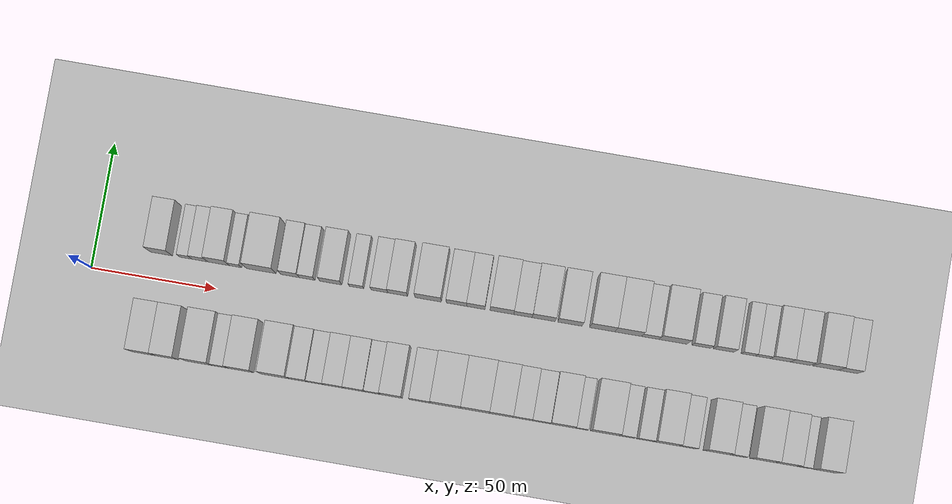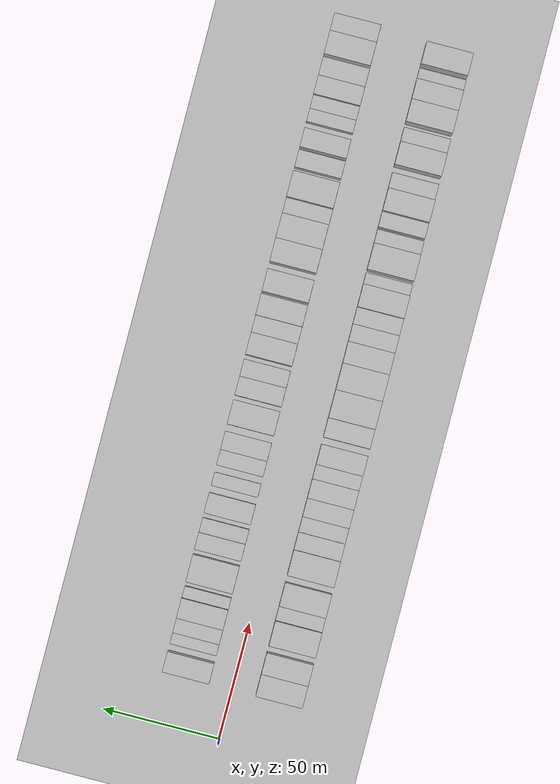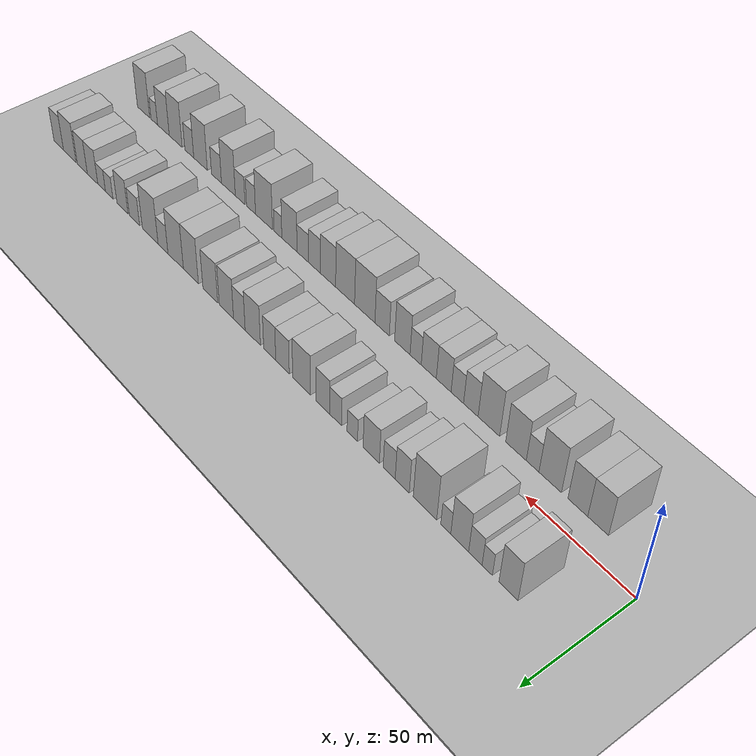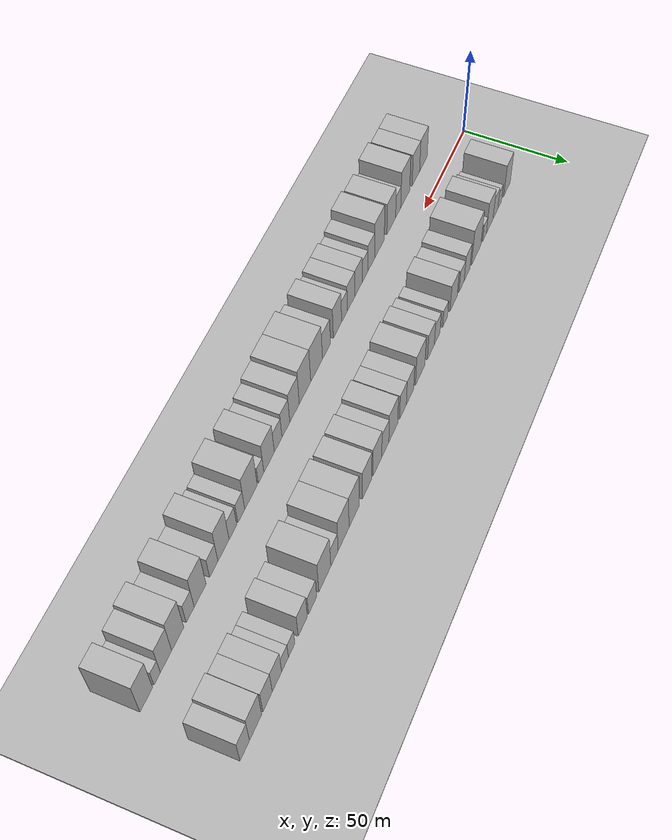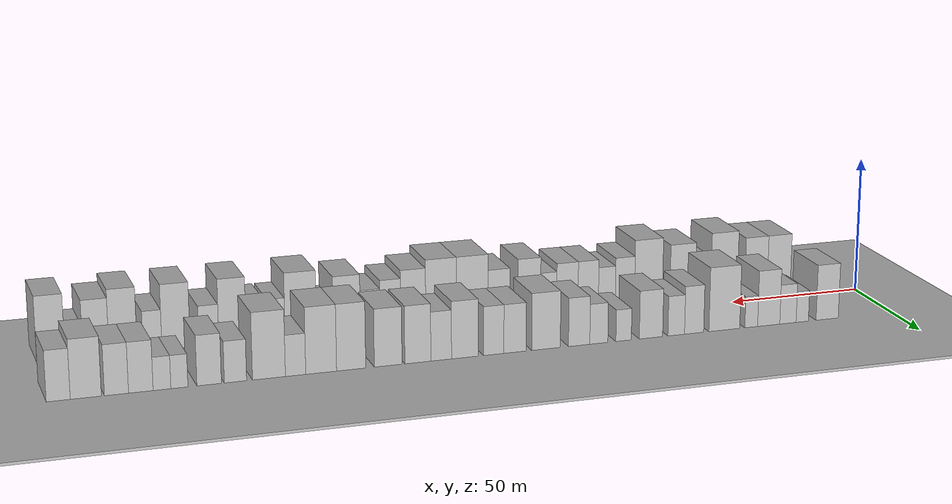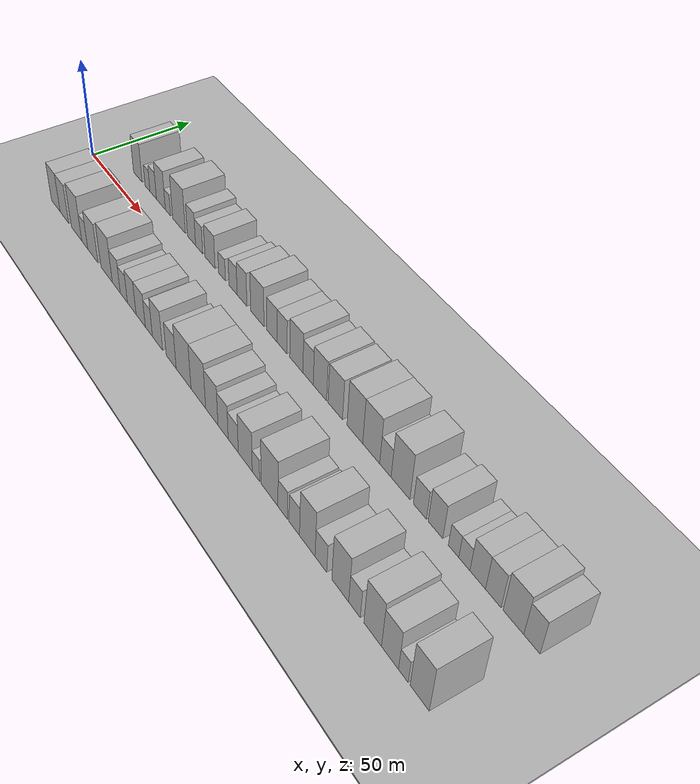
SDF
<?xml version="1.0" encoding="utf-8"?>

<sdf version="1.6">

   <world name="default">

      <gui fullscreen="0">

         <camera name="user_camera">

            <pose>-15 0 4.57585 0 0 0</pose>

            <view_controller>orbit</view_controller>

         </camera>

      </gui>

      <scene>

         <sky>

           <clouds>

             <speed>12</speed>

           </clouds>

         </sky>

         <ambient>0.4 0.4 0.4 1</ambient>

         <background>0.7 0.7 0.7 1</background>

         <shadows>1</shadows>

      </scene>

      <gravity>0 0 -9.8066</gravity>

      <magnetic_field>6e-06 2.3e-05 -4.2e-05</magnetic_field>

      <physics default="0" name="default_physics" type="ode">

         <ode>

            <solver>

               <type>quick</type>

               <iters>10</iters>

               <sor>1.0</sor>

               <use_dynamic_moi_rescaling>0</use_dynamic_moi_rescaling>

            </solver>

            <constraints>

               <cfm>0</cfm>

               <erp>0.2</erp>

               <contact_max_correcting_vel>100</contact_max_correcting_vel>

               <contact_surface_layer>0.001</contact_surface_layer>

            </constraints>

         </ode>

         <max_step_size>0.004</max_step_size>

         <real_time_factor>1</real_time_factor>

         <real_time_update_rate>250</real_time_update_rate>

      </physics>

      <light name="sun" type="directional">

         <cast_shadows>1</cast_shadows>

         <pose>0 0 10 0 0 0</pose>

         <diffuse>0.8 0.8 0.8 1</diffuse>

         <specular>0.2 0.2 0.2 1</specular>

         <attenuation>

            <range>1000</range>

            <constant>0.9</constant>

            <linear>0.01</linear>

            <quadratic>0.001</quadratic>

         </attenuation>

         <direction>-0.5 0.1 -0.9</direction>

      </light>

      <include>

         <name>ground_plane_1</name>

         <uri>model://HANNAS_ground_plane</uri>

         <pose>0 0 0  0 0 0</pose>

      </include>

      <include>

         <name>ground_plane_2</name>

         <uri>model://HANNAS_ground_plane</uri>

         <pose>100 0 0  0 0 0</pose>

      </include>

      <model name="building_1">

         <static>1</static>

         <pose frame="">26.3888 20.0000 0 0.000000 0.000000 1.570796</pose>

         <link name="link">

            <pose frame="">0 0 10.50 0 0 0</pose>

            <collision name="collision">

               <geometry>

                  <box>

                     <size>20.0000 8.7776 21.0000</size>

                  </box>

               </geometry>

               <max_contacts>10</max_contacts>

               <surface>

                  <contact>

                     <ode/>

                  </contact>

                  <bounce/>

                  <friction>

                     <torsional>

                        <ode/>

                     </torsional>

                     <ode/>

                  </friction>

               </surface>

            </collision>

            <visual name="visual">

               <cast_shadows>0</cast_shadows>

               <geometry>

                  <box>

                     <size>20.0000 8.7776 21.0000</size>

                  </box>

               </geometry>

               <material>

                  <script>

                     <uri>model://HANNAS_wall/materials/scripts</uri>

                     <uri>model://HANNAS_wall/materials/textures</uri>

                     <name>vrc/HANNAS_wall</name>

                  </script>

               </material>

            </visual>

            <self_collide>0</self_collide>

            <enable_wind>0</enable_wind>

            <kinematic>0</kinematic>

         </link>

      </model>

      <model name="building_2">

         <static>1</static>

         <pose frame="">36.1989 20.0000 0 0.000000 0.000000 1.570796</pose>

         <link name="link">

            <pose frame="">0 0 6.00 0 0 0</pose>

            <collision name="collision">

               <geometry>

                  <box>

                     <size>20.0000 4.8425 12.0000</size>

                  </box>

               </geometry>

               <max_contacts>10</max_contacts>

               <surface>

                  <contact>

                     <ode/>

                  </contact>

                  <bounce/>

                  <friction>

                     <torsional>

                        <ode/>

                     </torsional>

                     <ode/>

                  </friction>

               </surface>

            </collision>

            <visual name="visual">

               <cast_shadows>0</cast_shadows>

               <geometry>

                  <box>

                     <size>20.0000 4.8425 12.0000</size>

                  </box>

               </geometry>

               <material>

                  <script>

                     <uri>model://HANNAS_wall/materials/scripts</uri>

                     <uri>model://HANNAS_wall/materials/textures</uri>

                     <name>vrc/HANNAS_wall</name>

                  </script>

               </material>

            </visual>

            <self_collide>0</self_collide>

            <enable_wind>0</enable_wind>

            <kinematic>0</kinematic>

         </link>

      </model>

      <model name="building_3">

         <static>1</static>

         <pose frame="">41.8042 20.0000 0 0.000000 0.000000 1.570796</pose>

         <link name="link">

            <pose frame="">0 0 7.50 0 0 0</pose>

            <collision name="collision">

               <geometry>

                  <box>

                     <size>20.0000 6.3682 15.0000</size>

                  </box>

               </geometry>

               <max_contacts>10</max_contacts>

               <surface>

                  <contact>

                     <ode/>

                  </contact>

                  <bounce/>

                  <friction>

                     <torsional>

                        <ode/>

                     </torsional>

                     <ode/>

                  </friction>

               </surface>

            </collision>

            <visual name="visual">

               <cast_shadows>0</cast_shadows>

               <geometry>

                  <box>

                     <size>20.0000 6.3682 15.0000</size>

                  </box>

               </geometry>

               <material>

                  <script>

                     <uri>model://HANNAS_wall/materials/scripts</uri>

                     <uri>model://HANNAS_wall/materials/textures</uri>

                     <name>vrc/HANNAS_wall</name>

                  </script>

               </material>

            </visual>

            <self_collide>0</self_collide>

            <enable_wind>0</enable_wind>

            <kinematic>0</kinematic>

         </link>

      </model>

      <model name="building_4">

         <static>1</static>

         <pose frame="">49.3002 20.0000 0 0.000000 0.000000 1.570796</pose>

         <link name="link">

            <pose frame="">0 0 10.50 0 0 0</pose>

            <collision name="collision">

               <geometry>

                  <box>

                     <size>20.0000 8.6239 21.0000</size>

                  </box>

               </geometry>

               <max_contacts>10</max_contacts>

               <surface>

                  <contact>

                     <ode/>

                  </contact>

                  <bounce/>

                  <friction>

                     <torsional>

                        <ode/>

                     </torsional>

                     <ode/>

                  </friction>

               </surface>

            </collision>

            <visual name="visual">

               <cast_shadows>0</cast_shadows>

               <geometry>

                  <box>

                     <size>20.0000 8.6239 21.0000</size>

                  </box>

               </geometry>

               <material>

                  <script>

                     <uri>model://HANNAS_wall/materials/scripts</uri>

                     <uri>model://HANNAS_wall/materials/textures</uri>

                     <name>vrc/HANNAS_wall</name>

                  </script>

               </material>

            </visual>

            <self_collide>0</self_collide>

            <enable_wind>0</enable_wind>

            <kinematic>0</kinematic>

         </link>

      </model>

      <model name="building_5">

         <static>1</static>

         <pose frame="">56.0855 20.0000 0 0.000000 0.000000 1.570796</pose>

         <link name="link">

            <pose frame="">0 0 6.00 0 0 0</pose>

            <collision name="collision">

               <geometry>

                  <box>

                     <size>20.0000 4.9467 12.0000</size>

                  </box>

               </geometry>

               <max_contacts>10</max_contacts>

               <surface>

                  <contact>

                     <ode/>

                  </contact>

                  <bounce/>

                  <friction>

                     <torsional>

                        <ode/>

                     </torsional>

                     <ode/>

                  </friction>

               </surface>

            </collision>

            <visual name="visual">

               <cast_shadows>0</cast_shadows>

               <geometry>

                  <box>

                     <size>20.0000 4.9467 12.0000</size>

                  </box>

               </geometry>

               <material>

                  <script>

                     <uri>model://HANNAS_wall/materials/scripts</uri>

                     <uri>model://HANNAS_wall/materials/textures</uri>

                     <name>vrc/HANNAS_wall</name>

                  </script>

               </material>

            </visual>

            <self_collide>0</self_collide>

            <enable_wind>0</enable_wind>

            <kinematic>0</kinematic>

         </link>

      </model>

      <model name="building_6">

         <static>1</static>

         <pose frame="">66.4720 20.0000 0 0.000000 0.000000 1.570796</pose>

         <link name="link">

            <pose frame="">0 0 12.00 0 0 0</pose>

            <collision name="collision">

               <geometry>

                  <box>

                     <size>20.0000 11.8263 24.0000</size>

                  </box>

               </geometry>

               <max_contacts>10</max_contacts>

               <surface>

                  <contact>

                     <ode/>

                  </contact>

                  <bounce/>

                  <friction>

                     <torsional>

                        <ode/>

                     </torsional>

                     <ode/>

                  </friction>

               </surface>

            </collision>

            <visual name="visual">

               <cast_shadows>0</cast_shadows>

               <geometry>

                  <box>

                     <size>20.0000 11.8263 24.0000</size>

                  </box>

               </geometry>

               <material>

                  <script>

                     <uri>model://HANNAS_wall/materials/scripts</uri>

                     <uri>model://HANNAS_wall/materials/textures</uri>

                     <name>vrc/HANNAS_wall</name>

                  </script>

               </material>

            </visual>

            <self_collide>0</self_collide>

            <enable_wind>0</enable_wind>

            <kinematic>0</kinematic>

         </link>

      </model>

      <model name="building_7">

         <static>1</static>

         <pose frame="">78.0322 20.0000 0 0.000000 0.000000 1.570796</pose>

         <link name="link">

            <pose frame="">0 0 9.00 0 0 0</pose>

            <collision name="collision">

               <geometry>

                  <box>

                     <size>20.0000 7.2941 18.0000</size>

                  </box>

               </geometry>

               <max_contacts>10</max_contacts>

               <surface>

                  <contact>

                     <ode/>

                  </contact>

                  <bounce/>

                  <friction>

                     <torsional>

                        <ode/>

                     </torsional>

                     <ode/>

                  </friction>

               </surface>

            </collision>

            <visual name="visual">

               <cast_shadows>0</cast_shadows>

               <geometry>

                  <box>

                     <size>20.0000 7.2941 18.0000</size>

                  </box>

               </geometry>

               <material>

                  <script>

                     <uri>model://HANNAS_wall/materials/scripts</uri>

                     <uri>model://HANNAS_wall/materials/textures</uri>

                     <name>vrc/HANNAS_wall</name>

                  </script>

               </material>

            </visual>

            <self_collide>0</self_collide>

            <enable_wind>0</enable_wind>

            <kinematic>0</kinematic>

         </link>

      </model>

      <model name="building_8">

         <static>1</static>

         <pose frame="">84.8287 20.0000 0 0.000000 0.000000 1.570796</pose>

         <link name="link">

            <pose frame="">0 0 7.50 0 0 0</pose>

            <collision name="collision">

               <geometry>

                  <box>

                     <size>20.0000 6.2990 15.0000</size>

                  </box>

               </geometry>

               <max_contacts>10</max_contacts>

               <surface>

                  <contact>

                     <ode/>

                  </contact>

                  <bounce/>

                  <friction>

                     <torsional>

                        <ode/>

                     </torsional>

                     <ode/>

                  </friction>

               </surface>

            </collision>

            <visual name="visual">

               <cast_shadows>0</cast_shadows>

               <geometry>

                  <box>

                     <size>20.0000 6.2990 15.0000</size>

                  </box>

               </geometry>

               <material>

                  <script>

                     <uri>model://HANNAS_wall/materials/scripts</uri>

                     <uri>model://HANNAS_wall/materials/textures</uri>

                     <name>vrc/HANNAS_wall</name>

                  </script>

               </material>

            </visual>

            <self_collide>0</self_collide>

            <enable_wind>0</enable_wind>

            <kinematic>0</kinematic>

         </link>

      </model>

      <model name="building_9">

         <static>1</static>

         <pose frame="">94.3611 20.0000 0 0.000000 0.000000 1.570796</pose>

         <link name="link">

            <pose frame="">0 0 9.00 0 0 0</pose>

            <collision name="collision">

               <geometry>

                  <box>

                     <size>20.0000 8.7658 18.0000</size>

                  </box>

               </geometry>

               <max_contacts>10</max_contacts>

               <surface>

                  <contact>

                     <ode/>

                  </contact>

                  <bounce/>

                  <friction>

                     <torsional>

                        <ode/>

                     </torsional>

                     <ode/>

                  </friction>

               </surface>

            </collision>

            <visual name="visual">

               <cast_shadows>0</cast_shadows>

               <geometry>

                  <box>

                     <size>20.0000 8.7658 18.0000</size>

                  </box>

               </geometry>

               <material>

                  <script>

                     <uri>model://HANNAS_wall/materials/scripts</uri>

                     <uri>model://HANNAS_wall/materials/textures</uri>

                     <name>vrc/HANNAS_wall</name>

                  </script>

               </material>

            </visual>

            <self_collide>0</self_collide>

            <enable_wind>0</enable_wind>

            <kinematic>0</kinematic>

         </link>

      </model>

      <model name="building_10">

         <static>1</static>

         <pose frame="">104.6269 20.0000 0 0.000000 0.000000 1.570796</pose>

         <link name="link">

            <pose frame="">0 0 6.00 0 0 0</pose>

            <collision name="collision">

               <geometry>

                  <box>

                     <size>20.0000 5.7658 12.0000</size>

                  </box>

               </geometry>

               <max_contacts>10</max_contacts>

               <surface>

                  <contact>

                     <ode/>

                  </contact>

                  <bounce/>

                  <friction>

                     <torsional>

                        <ode/>

                     </torsional>

                     <ode/>

                  </friction>

               </surface>

            </collision>

            <visual name="visual">

               <cast_shadows>0</cast_shadows>

               <geometry>

                  <box>

                     <size>20.0000 5.7658 12.0000</size>

                  </box>

               </geometry>

               <material>

                  <script>

                     <uri>model://HANNAS_wall/materials/scripts</uri>

                     <uri>model://HANNAS_wall/materials/textures</uri>

                     <name>vrc/HANNAS_wall</name>

                  </script>

               </material>

            </visual>

            <self_collide>0</self_collide>

            <enable_wind>0</enable_wind>

            <kinematic>0</kinematic>

         </link>

      </model>

      <model name="building_11">

         <static>1</static>

         <pose frame="">113.8490 20.0000 0 0.000000 0.000000 1.570796</pose>

         <link name="link">

            <pose frame="">0 0 7.50 0 0 0</pose>

            <collision name="collision">

               <geometry>

                  <box>

                     <size>20.0000 6.6784 15.0000</size>

                  </box>

               </geometry>

               <max_contacts>10</max_contacts>

               <surface>

                  <contact>

                     <ode/>

                  </contact>

                  <bounce/>

                  <friction>

                     <torsional>

                        <ode/>

                     </torsional>

                     <ode/>

                  </friction>

               </surface>

            </collision>

            <visual name="visual">

               <cast_shadows>0</cast_shadows>

               <geometry>

                  <box>

                     <size>20.0000 6.6784 15.0000</size>

                  </box>

               </geometry>

               <material>

                  <script>

                     <uri>model://HANNAS_wall/materials/scripts</uri>

                     <uri>model://HANNAS_wall/materials/textures</uri>

                     <name>vrc/HANNAS_wall</name>

                  </script>

               </material>

            </visual>

            <self_collide>0</self_collide>

            <enable_wind>0</enable_wind>

            <kinematic>0</kinematic>

         </link>

      </model>

      <model name="building_12">

         <static>1</static>

         <pose frame="">121.1277 20.0000 0 0.000000 0.000000 1.570796</pose>

         <link name="link">

            <pose frame="">0 0 9.00 0 0 0</pose>

            <collision name="collision">

               <geometry>

                  <box>

                     <size>20.0000 7.8790 18.0000</size>

                  </box>

               </geometry>

               <max_contacts>10</max_contacts>

               <surface>

                  <contact>

                     <ode/>

                  </contact>

                  <bounce/>

                  <friction>

                     <torsional>

                        <ode/>

                     </torsional>

                     <ode/>

                  </friction>

               </surface>

            </collision>

            <visual name="visual">

               <cast_shadows>0</cast_shadows>

               <geometry>

                  <box>

                     <size>20.0000 7.8790 18.0000</size>

                  </box>

               </geometry>

               <material>

                  <script>

                     <uri>model://HANNAS_wall/materials/scripts</uri>

                     <uri>model://HANNAS_wall/materials/textures</uri>

                     <name>vrc/HANNAS_wall</name>

                  </script>

               </material>

            </visual>

            <self_collide>0</self_collide>

            <enable_wind>0</enable_wind>

            <kinematic>0</kinematic>

         </link>

      </model>

      <model name="building_13">

         <static>1</static>

         <pose frame="">133.2962 20.0000 0 0.000000 0.000000 1.570796</pose>

         <link name="link">

            <pose frame="">0 0 10.50 0 0 0</pose>

            <collision name="collision">

               <geometry>

                  <box>

                     <size>20.0000 10.4580 21.0000</size>

                  </box>

               </geometry>

               <max_contacts>10</max_contacts>

               <surface>

                  <contact>

                     <ode/>

                  </contact>

                  <bounce/>

                  <friction>

                     <torsional>

                        <ode/>

                     </torsional>

                     <ode/>

                  </friction>

               </surface>

            </collision>

            <visual name="visual">

               <cast_shadows>0</cast_shadows>

               <geometry>

                  <box>

                     <size>20.0000 10.4580 21.0000</size>

                  </box>

               </geometry>

               <material>

                  <script>

                     <uri>model://HANNAS_wall/materials/scripts</uri>

                     <uri>model://HANNAS_wall/materials/textures</uri>

                     <name>vrc/HANNAS_wall</name>

                  </script>

               </material>

            </visual>

            <self_collide>0</self_collide>

            <enable_wind>0</enable_wind>

            <kinematic>0</kinematic>

         </link>

      </model>

      <model name="building_14">

         <static>1</static>

         <pose frame="">144.5761 20.0000 0 0.000000 0.000000 1.570796</pose>

         <link name="link">

            <pose frame="">0 0 9.00 0 0 0</pose>

            <collision name="collision">

               <geometry>

                  <box>

                     <size>20.0000 8.1019 18.0000</size>

                  </box>

               </geometry>

               <max_contacts>10</max_contacts>

               <surface>

                  <contact>

                     <ode/>

                  </contact>

                  <bounce/>

                  <friction>

                     <torsional>

                        <ode/>

                     </torsional>

                     <ode/>

                  </friction>

               </surface>

            </collision>

            <visual name="visual">

               <cast_shadows>0</cast_shadows>

               <geometry>

                  <box>

                     <size>20.0000 8.1019 18.0000</size>

                  </box>

               </geometry>

               <material>

                  <script>

                     <uri>model://HANNAS_wall/materials/scripts</uri>

                     <uri>model://HANNAS_wall/materials/textures</uri>

                     <name>vrc/HANNAS_wall</name>

                  </script>

               </material>

            </visual>

            <self_collide>0</self_collide>

            <enable_wind>0</enable_wind>

            <kinematic>0</kinematic>

         </link>

      </model>

      <model name="building_15">

         <static>1</static>

         <pose frame="">152.2829 20.0000 0 0.000000 0.000000 1.570796</pose>

         <link name="link">

            <pose frame="">0 0 9.00 0 0 0</pose>

            <collision name="collision">

               <geometry>

                  <box>

                     <size>20.0000 7.3115 18.0000</size>

                  </box>

               </geometry>

               <max_contacts>10</max_contacts>

               <surface>

                  <contact>

                     <ode/>

                  </contact>

                  <bounce/>

                  <friction>

                     <torsional>

                        <ode/>

                     </torsional>

                     <ode/>

                  </friction>

               </surface>

            </collision>

            <visual name="visual">

               <cast_shadows>0</cast_shadows>

               <geometry>

                  <box>

                     <size>20.0000 7.3115 18.0000</size>

                  </box>

               </geometry>

               <material>

                  <script>

                     <uri>model://HANNAS_wall/materials/scripts</uri>

                     <uri>model://HANNAS_wall/materials/textures</uri>

                     <name>vrc/HANNAS_wall</name>

                  </script>

               </material>

            </visual>

            <self_collide>0</self_collide>

            <enable_wind>0</enable_wind>

            <kinematic>0</kinematic>

         </link>

      </model>

      <model name="building_16">

         <static>1</static>

         <pose frame="">162.6856 20.0000 0 0.000000 0.000000 1.570796</pose>

         <link name="link">

            <pose frame="">0 0 10.50 0 0 0</pose>

            <collision name="collision">

               <geometry>

                  <box>

                     <size>20.0000 9.4940 21.0000</size>

                  </box>

               </geometry>

               <max_contacts>10</max_contacts>

               <surface>

                  <contact>

                     <ode/>

                  </contact>

                  <bounce/>

                  <friction>

                     <torsional>

                        <ode/>

                     </torsional>

                     <ode/>

                  </friction>

               </surface>

            </collision>

            <visual name="visual">

               <cast_shadows>0</cast_shadows>

               <geometry>

                  <box>

                     <size>20.0000 9.4940 21.0000</size>

                  </box>

               </geometry>

               <material>

                  <script>

                     <uri>model://HANNAS_wall/materials/scripts</uri>

                     <uri>model://HANNAS_wall/materials/textures</uri>

                     <name>vrc/HANNAS_wall</name>

                  </script>

               </material>

            </visual>

            <self_collide>0</self_collide>

            <enable_wind>0</enable_wind>

            <kinematic>0</kinematic>

         </link>

      </model>

      <model name="building_17">

         <static>1</static>

         <pose frame="">171.1041 20.0000 0 0.000000 0.000000 1.570796</pose>

         <link name="link">

            <pose frame="">0 0 9.00 0 0 0</pose>

            <collision name="collision">

               <geometry>

                  <box>

                     <size>20.0000 7.3430 18.0000</size>

                  </box>

               </geometry>

               <max_contacts>10</max_contacts>

               <surface>

                  <contact>

                     <ode/>

                  </contact>

                  <bounce/>

                  <friction>

                     <torsional>

                        <ode/>

                     </torsional>

                     <ode/>

                  </friction>

               </surface>

            </collision>

            <visual name="visual">

               <cast_shadows>0</cast_shadows>

               <geometry>

                  <box>

                     <size>20.0000 7.3430 18.0000</size>

                  </box>

               </geometry>

               <material>

                  <script>

                     <uri>model://HANNAS_wall/materials/scripts</uri>

                     <uri>model://HANNAS_wall/materials/textures</uri>

                     <name>vrc/HANNAS_wall</name>

                  </script>

               </material>

            </visual>

            <self_collide>0</self_collide>

            <enable_wind>0</enable_wind>

            <kinematic>0</kinematic>

         </link>

      </model>

      <model name="building_18">

         <static>1</static>

         <pose frame="">179.3679 20.0000 0 0.000000 0.000000 1.570796</pose>

         <link name="link">

            <pose frame="">0 0 10.50 0 0 0</pose>

            <collision name="collision">

               <geometry>

                  <box>

                     <size>20.0000 9.1845 21.0000</size>

                  </box>

               </geometry>

               <max_contacts>10</max_contacts>

               <surface>

                  <contact>

                     <ode/>

                  </contact>

                  <bounce/>

                  <friction>

                     <torsional>

                        <ode/>

                     </torsional>

                     <ode/>

                  </friction>

               </surface>

            </collision>

            <visual name="visual">

               <cast_shadows>0</cast_shadows>

               <geometry>

                  <box>

                     <size>20.0000 9.1845 21.0000</size>

                  </box>

               </geometry>

               <material>

                  <script>

                     <uri>model://HANNAS_wall/materials/scripts</uri>

                     <uri>model://HANNAS_wall/materials/textures</uri>

                     <name>vrc/HANNAS_wall</name>

                  </script>

               </material>

            </visual>

            <self_collide>0</self_collide>

            <enable_wind>0</enable_wind>

            <kinematic>0</kinematic>

         </link>

      </model>

      <model name="building_19">

         <static>1</static>

         <pose frame="">189.8093 20.0000 0 0.000000 0.000000 1.570796</pose>

         <link name="link">

            <pose frame="">0 0 10.50 0 0 0</pose>

            <collision name="collision">

               <geometry>

                  <box>

                     <size>20.0000 9.6983 21.0000</size>

                  </box>

               </geometry>

               <max_contacts>10</max_contacts>

               <surface>

                  <contact>

                     <ode/>

                  </contact>

                  <bounce/>

                  <friction>

                     <torsional>

                        <ode/>

                     </torsional>

                     <ode/>

                  </friction>

               </surface>

            </collision>

            <visual name="visual">

               <cast_shadows>0</cast_shadows>

               <geometry>

                  <box>

                     <size>20.0000 9.6983 21.0000</size>

                  </box>

               </geometry>

               <material>

                  <script>

                     <uri>model://HANNAS_wall/materials/scripts</uri>

                     <uri>model://HANNAS_wall/materials/textures</uri>

                     <name>vrc/HANNAS_wall</name>

                  </script>

               </material>

            </visual>

            <self_collide>0</self_collide>

            <enable_wind>0</enable_wind>

            <kinematic>0</kinematic>

         </link>

      </model>

      <model name="building_20">

         <static>1</static>

         <pose frame="">202.7111 20.0000 0 0.000000 0.000000 1.570796</pose>

         <link name="link">

            <pose frame="">0 0 12.00 0 0 0</pose>

            <collision name="collision">

               <geometry>

                  <box>

                     <size>20.0000 10.1054 24.0000</size>

                  </box>

               </geometry>

               <max_contacts>10</max_contacts>

               <surface>

                  <contact>

                     <ode/>

                  </contact>

                  <bounce/>

                  <friction>

                     <torsional>

                        <ode/>

                     </torsional>

                     <ode/>

                  </friction>

               </surface>

            </collision>

            <visual name="visual">

               <cast_shadows>0</cast_shadows>

               <geometry>

                  <box>

                     <size>20.0000 10.1054 24.0000</size>

                  </box>

               </geometry>

               <material>

                  <script>

                     <uri>model://HANNAS_wall/materials/scripts</uri>

                     <uri>model://HANNAS_wall/materials/textures</uri>

                     <name>vrc/HANNAS_wall</name>

                  </script>

               </material>

            </visual>

            <self_collide>0</self_collide>

            <enable_wind>0</enable_wind>

            <kinematic>0</kinematic>

         </link>

      </model>

      <model name="building_21">

         <static>1</static>

         <pose frame="">213.0783 20.0000 0 0.000000 0.000000 1.570796</pose>

         <link name="link">

            <pose frame="">0 0 12.00 0 0 0</pose>

            <collision name="collision">

               <geometry>

                  <box>

                     <size>20.0000 10.6290 24.0000</size>

                  </box>

               </geometry>

               <max_contacts>10</max_contacts>

               <surface>

                  <contact>

                     <ode/>

                  </contact>

                  <bounce/>

                  <friction>

                     <torsional>

                        <ode/>

                     </torsional>

                     <ode/>

                  </friction>

               </surface>

            </collision>

            <visual name="visual">

               <cast_shadows>0</cast_shadows>

               <geometry>

                  <box>

                     <size>20.0000 10.6290 24.0000</size>

                  </box>

               </geometry>

               <material>

                  <script>

                     <uri>model://HANNAS_wall/materials/scripts</uri>

                     <uri>model://HANNAS_wall/materials/textures</uri>

                     <name>vrc/HANNAS_wall</name>

                  </script>

               </material>

            </visual>

            <self_collide>0</self_collide>

            <enable_wind>0</enable_wind>

            <kinematic>0</kinematic>

         </link>

      </model>

      <model name="building_22">

         <static>1</static>

         <pose frame="">221.8662 20.0000 0 0.000000 0.000000 1.570796</pose>

         <link name="link">

            <pose frame="">0 0 7.50 0 0 0</pose>

            <collision name="collision">

               <geometry>

                  <box>

                     <size>20.0000 6.9468 15.0000</size>

                  </box>

               </geometry>

               <max_contacts>10</max_contacts>

               <surface>

                  <contact>

                     <ode/>

                  </contact>

                  <bounce/>

                  <friction>

                     <torsional>

                        <ode/>

                     </torsional>

                     <ode/>

                  </friction>

               </surface>

            </collision>

            <visual name="visual">

               <cast_shadows>0</cast_shadows>

               <geometry>

                  <box>

                     <size>20.0000 6.9468 15.0000</size>

                  </box>

               </geometry>

               <material>

                  <script>

                     <uri>model://HANNAS_wall/materials/scripts</uri>

                     <uri>model://HANNAS_wall/materials/textures</uri>

                     <name>vrc/HANNAS_wall</name>

                  </script>

               </material>

            </visual>

            <self_collide>0</self_collide>

            <enable_wind>0</enable_wind>

            <kinematic>0</kinematic>

         </link>

      </model>

      <model name="building_23">

         <static>1</static>

         <pose frame="">230.9216 20.0000 0 0.000000 0.000000 1.570796</pose>

         <link name="link">

            <pose frame="">0 0 12.00 0 0 0</pose>

            <collision name="collision">

               <geometry>

                  <box>

                     <size>20.0000 11.1640 24.0000</size>

                  </box>

               </geometry>

               <max_contacts>10</max_contacts>

               <surface>

                  <contact>

                     <ode/>

                  </contact>

                  <bounce/>

                  <friction>

                     <torsional>

                        <ode/>

                     </torsional>

                     <ode/>

                  </friction>

               </surface>

            </collision>

            <visual name="visual">

               <cast_shadows>0</cast_shadows>

               <geometry>

                  <box>

                     <size>20.0000 11.1640 24.0000</size>

                  </box>

               </geometry>

               <material>

                  <script>

                     <uri>model://HANNAS_wall/materials/scripts</uri>

                     <uri>model://HANNAS_wall/materials/textures</uri>

                     <name>vrc/HANNAS_wall</name>

                  </script>

               </material>

            </visual>

            <self_collide>0</self_collide>

            <enable_wind>0</enable_wind>

            <kinematic>0</kinematic>

         </link>

      </model>

      <model name="building_24">

         <static>1</static>

         <pose frame="">242.2442 20.0000 0 0.000000 0.000000 1.570796</pose>

         <link name="link">

            <pose frame="">0 0 7.50 0 0 0</pose>

            <collision name="collision">

               <geometry>

                  <box>

                     <size>20.0000 7.4812 15.0000</size>

                  </box>

               </geometry>

               <max_contacts>10</max_contacts>

               <surface>

                  <contact>

                     <ode/>

                  </contact>

                  <bounce/>

                  <friction>

                     <torsional>

                        <ode/>

                     </torsional>

                     <ode/>

                  </friction>

               </surface>

            </collision>

            <visual name="visual">

               <cast_shadows>0</cast_shadows>

               <geometry>

                  <box>

                     <size>20.0000 7.4812 15.0000</size>

                  </box>

               </geometry>

               <material>

                  <script>

                     <uri>model://HANNAS_wall/materials/scripts</uri>

                     <uri>model://HANNAS_wall/materials/textures</uri>

                     <name>vrc/HANNAS_wall</name>

                  </script>

               </material>

            </visual>

            <self_collide>0</self_collide>

            <enable_wind>0</enable_wind>

            <kinematic>0</kinematic>

         </link>

      </model>

      <model name="building_25">

         <static>1</static>

         <pose frame="">251.0758 20.0000 0 0.000000 0.000000 1.570796</pose>

         <link name="link">

            <pose frame="">0 0 9.00 0 0 0</pose>

            <collision name="collision">

               <geometry>

                  <box>

                     <size>20.0000 8.1820 18.0000</size>

                  </box>

               </geometry>

               <max_contacts>10</max_contacts>

               <surface>

                  <contact>

                     <ode/>

                  </contact>

                  <bounce/>

                  <friction>

                     <torsional>

                        <ode/>

                     </torsional>

                     <ode/>

                  </friction>

               </surface>

            </collision>

            <visual name="visual">

               <cast_shadows>0</cast_shadows>

               <geometry>

                  <box>

                     <size>20.0000 8.1820 18.0000</size>

                  </box>

               </geometry>

               <material>

                  <script>

                     <uri>model://HANNAS_wall/materials/scripts</uri>

                     <uri>model://HANNAS_wall/materials/textures</uri>

                     <name>vrc/HANNAS_wall</name>

                  </script>

               </material>

            </visual>

            <self_collide>0</self_collide>

            <enable_wind>0</enable_wind>

            <kinematic>0</kinematic>

         </link>

      </model>

      <model name="building_26">

         <static>1</static>

         <pose frame="">260.9896 20.0000 0 0.000000 0.000000 1.570796</pose>

         <link name="link">

            <pose frame="">0 0 6.00 0 0 0</pose>

            <collision name="collision">

               <geometry>

                  <box>

                     <size>20.0000 5.6456 12.0000</size>

                  </box>

               </geometry>

               <max_contacts>10</max_contacts>

               <surface>

                  <contact>

                     <ode/>

                  </contact>

                  <bounce/>

                  <friction>

                     <torsional>

                        <ode/>

                     </torsional>

                     <ode/>

                  </friction>

               </surface>

            </collision>

            <visual name="visual">

               <cast_shadows>0</cast_shadows>

               <geometry>

                  <box>

                     <size>20.0000 5.6456 12.0000</size>

                  </box>

               </geometry>

               <material>

                  <script>

                     <uri>model://HANNAS_wall/materials/scripts</uri>

                     <uri>model://HANNAS_wall/materials/textures</uri>

                     <name>vrc/HANNAS_wall</name>

                  </script>

               </material>

            </visual>

            <self_collide>0</self_collide>

            <enable_wind>0</enable_wind>

            <kinematic>0</kinematic>

         </link>

      </model>

      <model name="building_27">

         <static>1</static>

         <pose frame="">266.7428 20.0000 0 0.000000 0.000000 1.570796</pose>

         <link name="link">

            <pose frame="">0 0 6.00 0 0 0</pose>

            <collision name="collision">

               <geometry>

                  <box>

                     <size>20.0000 5.8609 12.0000</size>

                  </box>

               </geometry>

               <max_contacts>10</max_contacts>

               <surface>

                  <contact>

                     <ode/>

                  </contact>

                  <bounce/>

                  <friction>

                     <torsional>

                        <ode/>

                     </torsional>

                     <ode/>

                  </friction>

               </surface>

            </collision>

            <visual name="visual">

               <cast_shadows>0</cast_shadows>

               <geometry>

                  <box>

                     <size>20.0000 5.8609 12.0000</size>

                  </box>

               </geometry>

               <material>

                  <script>

                     <uri>model://HANNAS_wall/materials/scripts</uri>

                     <uri>model://HANNAS_wall/materials/textures</uri>

                     <name>vrc/HANNAS_wall</name>

                  </script>

               </material>

            </visual>

            <self_collide>0</self_collide>

            <enable_wind>0</enable_wind>

            <kinematic>0</kinematic>

         </link>

      </model>

      <model name="building_28">

         <static>1</static>

         <pose frame="">273.7163 20.0000 0 0.000000 0.000000 1.570796</pose>

         <link name="link">

            <pose frame="">0 0 9.00 0 0 0</pose>

            <collision name="collision">

               <geometry>

                  <box>

                     <size>20.0000 8.0861 18.0000</size>

                  </box>

               </geometry>

               <max_contacts>10</max_contacts>

               <surface>

                  <contact>

                     <ode/>

                  </contact>

                  <bounce/>

                  <friction>

                     <torsional>

                        <ode/>

                     </torsional>

                     <ode/>

                  </friction>

               </surface>

            </collision>

            <visual name="visual">

               <cast_shadows>0</cast_shadows>

               <geometry>

                  <box>

                     <size>20.0000 8.0861 18.0000</size>

                  </box>

               </geometry>

               <material>

                  <script>

                     <uri>model://HANNAS_wall/materials/scripts</uri>

                     <uri>model://HANNAS_wall/materials/textures</uri>

                     <name>vrc/HANNAS_wall</name>

                  </script>

               </material>

            </visual>

            <self_collide>0</self_collide>

            <enable_wind>0</enable_wind>

            <kinematic>0</kinematic>

         </link>

      </model>

      <model name="building_29">

         <static>1</static>

         <pose frame="">281.6931 20.0000 0 0.000000 0.000000 1.570796</pose>

         <link name="link">

            <pose frame="">0 0 9.00 0 0 0</pose>

            <collision name="collision">

               <geometry>

                  <box>

                     <size>20.0000 7.8675 18.0000</size>

                  </box>

               </geometry>

               <max_contacts>10</max_contacts>

               <surface>

                  <contact>

                     <ode/>

                  </contact>

                  <bounce/>

                  <friction>

                     <torsional>

                        <ode/>

                     </torsional>

                     <ode/>

                  </friction>

               </surface>

            </collision>

            <visual name="visual">

               <cast_shadows>0</cast_shadows>

               <geometry>

                  <box>

                     <size>20.0000 7.8675 18.0000</size>

                  </box>

               </geometry>

               <material>

                  <script>

                     <uri>model://HANNAS_wall/materials/scripts</uri>

                     <uri>model://HANNAS_wall/materials/textures</uri>

                     <name>vrc/HANNAS_wall</name>

                  </script>

               </material>

            </visual>

            <self_collide>0</self_collide>

            <enable_wind>0</enable_wind>

            <kinematic>0</kinematic>

         </link>

      </model>

      <model name="building_30">

         <static>1</static>

         <pose frame="">291.6609 20.0000 0 0.000000 0.000000 1.570796</pose>

         <link name="link">

            <pose frame="">0 0 10.50 0 0 0</pose>

            <collision name="collision">

               <geometry>

                  <box>

                     <size>20.0000 10.0680 21.0000</size>

                  </box>

               </geometry>

               <max_contacts>10</max_contacts>

               <surface>

                  <contact>

                     <ode/>

                  </contact>

                  <bounce/>

                  <friction>

                     <torsional>

                        <ode/>

                     </torsional>

                     <ode/>

                  </friction>

               </surface>

            </collision>

            <visual name="visual">

               <cast_shadows>0</cast_shadows>

               <geometry>

                  <box>

                     <size>20.0000 10.0680 21.0000</size>

                  </box>

               </geometry>

               <material>

                  <script>

                     <uri>model://HANNAS_wall/materials/scripts</uri>

                     <uri>model://HANNAS_wall/materials/textures</uri>

                     <name>vrc/HANNAS_wall</name>

                  </script>

               </material>

            </visual>

            <self_collide>0</self_collide>

            <enable_wind>0</enable_wind>

            <kinematic>0</kinematic>

         </link>

      </model>

      <model name="building_31">

         <static>1</static>

         <pose frame="">300.5624 20.0000 0 0.000000 0.000000 1.570796</pose>

         <link name="link">

            <pose frame="">0 0 9.00 0 0 0</pose>

            <collision name="collision">

               <geometry>

                  <box>

                     <size>20.0000 7.7350 18.0000</size>

                  </box>

               </geometry>

               <max_contacts>10</max_contacts>

               <surface>

                  <contact>

                     <ode/>

                  </contact>

                  <bounce/>

                  <friction>

                     <torsional>

                        <ode/>

                     </torsional>

                     <ode/>

                  </friction>

               </surface>

            </collision>

            <visual name="visual">

               <cast_shadows>0</cast_shadows>

               <geometry>

                  <box>

                     <size>20.0000 7.7350 18.0000</size>

                  </box>

               </geometry>

               <material>

                  <script>

                     <uri>model://HANNAS_wall/materials/scripts</uri>

                     <uri>model://HANNAS_wall/materials/textures</uri>

                     <name>vrc/HANNAS_wall</name>

                  </script>

               </material>

            </visual>

            <self_collide>0</self_collide>

            <enable_wind>0</enable_wind>

            <kinematic>0</kinematic>

         </link>

      </model>

      <model name="building_32">

         <static>1</static>

         <pose frame="">26.7276 -20.0000 0 0.000000 0.000000 1.570796</pose>

         <link name="link">

            <pose frame="">0 0 10.50 0 0 0</pose>

            <collision name="collision">

               <geometry>

                  <box>

                     <size>20.0000 9.4552 21.0000</size>

                  </box>

               </geometry>

               <max_contacts>10</max_contacts>

               <surface>

                  <contact>

                     <ode/>

                  </contact>

                  <bounce/>

                  <friction>

                     <torsional>

                        <ode/>

                     </torsional>

                     <ode/>

                  </friction>

               </surface>

            </collision>

            <visual name="visual">

               <cast_shadows>0</cast_shadows>

               <geometry>

                  <box>

                     <size>20.0000 9.4552 21.0000</size>

                  </box>

               </geometry>

               <material>

                  <script>

                     <uri>model://HANNAS_wall/materials/scripts</uri>

                     <uri>model://HANNAS_wall/materials/textures</uri>

                     <name>vrc/HANNAS_wall</name>

                  </script>

               </material>

            </visual>

            <self_collide>0</self_collide>

            <enable_wind>0</enable_wind>

            <kinematic>0</kinematic>

         </link>

      </model>

      <model name="building_33">

         <static>1</static>

         <pose frame="">36.0451 -20.0000 0 0.000000 0.000000 1.570796</pose>

         <link name="link">

            <pose frame="">0 0 10.50 0 0 0</pose>

            <collision name="collision">

               <geometry>

                  <box>

                     <size>20.0000 9.1799 21.0000</size>

                  </box>

               </geometry>

               <max_contacts>10</max_contacts>

               <surface>

                  <contact>

                     <ode/>

                  </contact>

                  <bounce/>

                  <friction>

                     <torsional>

                        <ode/>

                     </torsional>

                     <ode/>

                  </friction>

               </surface>

            </collision>

            <visual name="visual">

               <cast_shadows>0</cast_shadows>

               <geometry>

                  <box>

                     <size>20.0000 9.1799 21.0000</size>

                  </box>

               </geometry>

               <material>

                  <script>

                     <uri>model://HANNAS_wall/materials/scripts</uri>

                     <uri>model://HANNAS_wall/materials/textures</uri>

                     <name>vrc/HANNAS_wall</name>

                  </script>

               </material>

            </visual>

            <self_collide>0</self_collide>

            <enable_wind>0</enable_wind>

            <kinematic>0</kinematic>

         </link>

      </model>

      <model name="building_34">

         <static>1</static>

         <pose frame="">49.0089 -20.0000 0 0.000000 0.000000 1.570796</pose>

         <link name="link">

            <pose frame="">0 0 12.00 0 0 0</pose>

            <collision name="collision">

               <geometry>

                  <box>

                     <size>20.0000 10.7476 24.0000</size>

                  </box>

               </geometry>

               <max_contacts>10</max_contacts>

               <surface>

                  <contact>

                     <ode/>

                  </contact>

                  <bounce/>

                  <friction>

                     <torsional>

                        <ode/>

                     </torsional>

                     <ode/>

                  </friction>

               </surface>

            </collision>

            <visual name="visual">

               <cast_shadows>0</cast_shadows>

               <geometry>

                  <box>

                     <size>20.0000 10.7476 24.0000</size>

                  </box>

               </geometry>

               <material>

                  <script>

                     <uri>model://HANNAS_wall/materials/scripts</uri>

                     <uri>model://HANNAS_wall/materials/textures</uri>

                     <name>vrc/HANNAS_wall</name>

                  </script>

               </material>

            </visual>

            <self_collide>0</self_collide>

            <enable_wind>0</enable_wind>

            <kinematic>0</kinematic>

         </link>

      </model>

      <model name="building_35">

         <static>1</static>

         <pose frame="">57.4555 -20.0000 0 0.000000 0.000000 1.570796</pose>

         <link name="link">

            <pose frame="">0 0 7.50 0 0 0</pose>

            <collision name="collision">

               <geometry>

                  <box>

                     <size>20.0000 6.1455 15.0000</size>

                  </box>

               </geometry>

               <max_contacts>10</max_contacts>

               <surface>

                  <contact>

                     <ode/>

                  </contact>

                  <bounce/>

                  <friction>

                     <torsional>

                        <ode/>

                     </torsional>

                     <ode/>

                  </friction>

               </surface>

            </collision>

            <visual name="visual">

               <cast_shadows>0</cast_shadows>

               <geometry>

                  <box>

                     <size>20.0000 6.1455 15.0000</size>

                  </box>

               </geometry>

               <material>

                  <script>

                     <uri>model://HANNAS_wall/materials/scripts</uri>

                     <uri>model://HANNAS_wall/materials/textures</uri>

                     <name>vrc/HANNAS_wall</name>

                  </script>

               </material>

            </visual>

            <self_collide>0</self_collide>

            <enable_wind>0</enable_wind>

            <kinematic>0</kinematic>

         </link>

      </model>

      <model name="building_36">

         <static>1</static>

         <pose frame="">65.6243 -20.0000 0 0.000000 0.000000 1.570796</pose>

         <link name="link">

            <pose frame="">0 0 10.50 0 0 0</pose>

            <collision name="collision">

               <geometry>

                  <box>

                     <size>20.0000 10.1923 21.0000</size>

                  </box>

               </geometry>

               <max_contacts>10</max_contacts>

               <surface>

                  <contact>

                     <ode/>

                  </contact>

                  <bounce/>

                  <friction>

                     <torsional>

                        <ode/>

                     </torsional>

                     <ode/>

                  </friction>

               </surface>

            </collision>

            <visual name="visual">

               <cast_shadows>0</cast_shadows>

               <geometry>

                  <box>

                     <size>20.0000 10.1923 21.0000</size>

                  </box>

               </geometry>

               <material>

                  <script>

                     <uri>model://HANNAS_wall/materials/scripts</uri>

                     <uri>model://HANNAS_wall/materials/textures</uri>

                     <name>vrc/HANNAS_wall</name>

                  </script>

               </material>

            </visual>

            <self_collide>0</self_collide>

            <enable_wind>0</enable_wind>

            <kinematic>0</kinematic>

         </link>

      </model>

      <model name="building_37">

         <static>1</static>

         <pose frame="">79.2264 -20.0000 0 0.000000 0.000000 1.570796</pose>

         <link name="link">

            <pose frame="">0 0 12.00 0 0 0</pose>

            <collision name="collision">

               <geometry>

                  <box>

                     <size>20.0000 11.0119 24.0000</size>

                  </box>

               </geometry>

               <max_contacts>10</max_contacts>

               <surface>

                  <contact>

                     <ode/>

                  </contact>

                  <bounce/>

                  <friction>

                     <torsional>

                        <ode/>

                     </torsional>

                     <ode/>

                  </friction>

               </surface>

            </collision>

            <visual name="visual">

               <cast_shadows>0</cast_shadows>

               <geometry>

                  <box>

                     <size>20.0000 11.0119 24.0000</size>

                  </box>

               </geometry>

               <material>

                  <script>

                     <uri>model://HANNAS_wall/materials/scripts</uri>

                     <uri>model://HANNAS_wall/materials/textures</uri>

                     <name>vrc/HANNAS_wall</name>

                  </script>

               </material>

            </visual>

            <self_collide>0</self_collide>

            <enable_wind>0</enable_wind>

            <kinematic>0</kinematic>

         </link>

      </model>

      <model name="building_38">

         <static>1</static>

         <pose frame="">88.5035 -20.0000 0 0.000000 0.000000 1.570796</pose>

         <link name="link">

            <pose frame="">0 0 9.00 0 0 0</pose>

            <collision name="collision">

               <geometry>

                  <box>

                     <size>20.0000 7.5423 18.0000</size>

                  </box>

               </geometry>

               <max_contacts>10</max_contacts>

               <surface>

                  <contact>

                     <ode/>

                  </contact>

                  <bounce/>

                  <friction>

                     <torsional>

                        <ode/>

                     </torsional>

                     <ode/>

                  </friction>

               </surface>

            </collision>

            <visual name="visual">

               <cast_shadows>0</cast_shadows>

               <geometry>

                  <box>

                     <size>20.0000 7.5423 18.0000</size>

                  </box>

               </geometry>

               <material>

                  <script>

                     <uri>model://HANNAS_wall/materials/scripts</uri>

                     <uri>model://HANNAS_wall/materials/textures</uri>

                     <name>vrc/HANNAS_wall</name>

                  </script>

               </material>

            </visual>

            <self_collide>0</self_collide>

            <enable_wind>0</enable_wind>

            <kinematic>0</kinematic>

         </link>

      </model>

      <model name="building_39">

         <static>1</static>

         <pose frame="">95.5723 -20.0000 0 0.000000 0.000000 1.570796</pose>

         <link name="link">

            <pose frame="">0 0 7.50 0 0 0</pose>

            <collision name="collision">

               <geometry>

                  <box>

                     <size>20.0000 6.5952 15.0000</size>

                  </box>

               </geometry>

               <max_contacts>10</max_contacts>

               <surface>

                  <contact>

                     <ode/>

                  </contact>

                  <bounce/>

                  <friction>

                     <torsional>

                        <ode/>

                     </torsional>

                     <ode/>

                  </friction>

               </surface>

            </collision>

            <visual name="visual">

               <cast_shadows>0</cast_shadows>

               <geometry>

                  <box>

                     <size>20.0000 6.5952 15.0000</size>

                  </box>

               </geometry>

               <material>

                  <script>

                     <uri>model://HANNAS_wall/materials/scripts</uri>

                     <uri>model://HANNAS_wall/materials/textures</uri>

                     <name>vrc/HANNAS_wall</name>

                  </script>

               </material>

            </visual>

            <self_collide>0</self_collide>

            <enable_wind>0</enable_wind>

            <kinematic>0</kinematic>

         </link>

      </model>

      <model name="building_40">

         <static>1</static>

         <pose frame="">102.8323 -20.0000 0 0.000000 0.000000 1.570796</pose>

         <link name="link">

            <pose frame="">0 0 9.00 0 0 0</pose>

            <collision name="collision">

               <geometry>

                  <box>

                     <size>20.0000 7.9248 18.0000</size>

                  </box>

               </geometry>

               <max_contacts>10</max_contacts>

               <surface>

                  <contact>

                     <ode/>

                  </contact>

                  <bounce/>

                  <friction>

                     <torsional>

                        <ode/>

                     </torsional>

                     <ode/>

                  </friction>

               </surface>

            </collision>

            <visual name="visual">

               <cast_shadows>0</cast_shadows>

               <geometry>

                  <box>

                     <size>20.0000 7.9248 18.0000</size>

                  </box>

               </geometry>

               <material>

                  <script>

                     <uri>model://HANNAS_wall/materials/scripts</uri>

                     <uri>model://HANNAS_wall/materials/textures</uri>

                     <name>vrc/HANNAS_wall</name>

                  </script>

               </material>

            </visual>

            <self_collide>0</self_collide>

            <enable_wind>0</enable_wind>

            <kinematic>0</kinematic>

         </link>

      </model>

      <model name="building_41">

         <static>1</static>

         <pose frame="">110.9113 -20.0000 0 0.000000 0.000000 1.570796</pose>

         <link name="link">

            <pose frame="">0 0 9.00 0 0 0</pose>

            <collision name="collision">

               <geometry>

                  <box>

                     <size>20.0000 8.2333 18.0000</size>

                  </box>

               </geometry>

               <max_contacts>10</max_contacts>

               <surface>

                  <contact>

                     <ode/>

                  </contact>

                  <bounce/>

                  <friction>

                     <torsional>

                        <ode/>

                     </torsional>

                     <ode/>

                  </friction>

               </surface>

            </collision>

            <visual name="visual">

               <cast_shadows>0</cast_shadows>

               <geometry>

                  <box>

                     <size>20.0000 8.2333 18.0000</size>

                  </box>

               </geometry>

               <material>

                  <script>

                     <uri>model://HANNAS_wall/materials/scripts</uri>

                     <uri>model://HANNAS_wall/materials/textures</uri>

                     <name>vrc/HANNAS_wall</name>

                  </script>

               </material>

            </visual>

            <self_collide>0</self_collide>

            <enable_wind>0</enable_wind>

            <kinematic>0</kinematic>

         </link>

      </model>

      <model name="building_42">

         <static>1</static>

         <pose frame="">118.1286 -20.0000 0 0.000000 0.000000 1.570796</pose>

         <link name="link">

            <pose frame="">0 0 7.50 0 0 0</pose>

            <collision name="collision">

               <geometry>

                  <box>

                     <size>20.0000 6.2013 15.0000</size>

                  </box>

               </geometry>

               <max_contacts>10</max_contacts>

               <surface>

                  <contact>

                     <ode/>

                  </contact>

                  <bounce/>

                  <friction>

                     <torsional>

                        <ode/>

                     </torsional>

                     <ode/>

                  </friction>

               </surface>

            </collision>

            <visual name="visual">

               <cast_shadows>0</cast_shadows>

               <geometry>

                  <box>

                     <size>20.0000 6.2013 15.0000</size>

                  </box>

               </geometry>

               <material>

                  <script>

                     <uri>model://HANNAS_wall/materials/scripts</uri>

                     <uri>model://HANNAS_wall/materials/textures</uri>

                     <name>vrc/HANNAS_wall</name>

                  </script>

               </material>

            </visual>

            <self_collide>0</self_collide>

            <enable_wind>0</enable_wind>

            <kinematic>0</kinematic>

         </link>

      </model>

      <model name="building_43">

         <static>1</static>

         <pose frame="">125.5785 -20.0000 0 0.000000 0.000000 1.570796</pose>

         <link name="link">

            <pose frame="">0 0 10.50 0 0 0</pose>

            <collision name="collision">

               <geometry>

                  <box>

                     <size>20.0000 8.6984 21.0000</size>

                  </box>

               </geometry>

               <max_contacts>10</max_contacts>

               <surface>

                  <contact>

                     <ode/>

                  </contact>

                  <bounce/>

                  <friction>

                     <torsional>

                        <ode/>

                     </torsional>

                     <ode/>

                  </friction>

               </surface>

            </collision>

            <visual name="visual">

               <cast_shadows>0</cast_shadows>

               <geometry>

                  <box>

                     <size>20.0000 8.6984 21.0000</size>

                  </box>

               </geometry>

               <material>

                  <script>

                     <uri>model://HANNAS_wall/materials/scripts</uri>

                     <uri>model://HANNAS_wall/materials/textures</uri>

                     <name>vrc/HANNAS_wall</name>

                  </script>

               </material>

            </visual>

            <self_collide>0</self_collide>

            <enable_wind>0</enable_wind>

            <kinematic>0</kinematic>

         </link>

      </model>

      <model name="building_44">

         <static>1</static>

         <pose frame="">137.0789 -20.0000 0 0.000000 0.000000 1.570796</pose>

         <link name="link">

            <pose frame="">0 0 9.00 0 0 0</pose>

            <collision name="collision">

               <geometry>

                  <box>

                     <size>20.0000 8.3025 18.0000</size>

                  </box>

               </geometry>

               <max_contacts>10</max_contacts>

               <surface>

                  <contact>

                     <ode/>

                  </contact>

                  <bounce/>

                  <friction>

                     <torsional>

                        <ode/>

                     </torsional>

                     <ode/>

                  </friction>

               </surface>

            </collision>

            <visual name="visual">

               <cast_shadows>0</cast_shadows>

               <geometry>

                  <box>

                     <size>20.0000 8.3025 18.0000</size>

                  </box>

               </geometry>

               <material>

                  <script>

                     <uri>model://HANNAS_wall/materials/scripts</uri>

                     <uri>model://HANNAS_wall/materials/textures</uri>

                     <name>vrc/HANNAS_wall</name>

                  </script>

               </material>

            </visual>

            <self_collide>0</self_collide>

            <enable_wind>0</enable_wind>

            <kinematic>0</kinematic>

         </link>

      </model>

      <model name="building_45">

         <static>1</static>

         <pose frame="">147.2234 -20.0000 0 0.000000 0.000000 1.570796</pose>

         <link name="link">

            <pose frame="">0 0 12.00 0 0 0</pose>

            <collision name="collision">

               <geometry>

                  <box>

                     <size>20.0000 11.9864 24.0000</size>

                  </box>

               </geometry>

               <max_contacts>10</max_contacts>

               <surface>

                  <contact>

                     <ode/>

                  </contact>

                  <bounce/>

                  <friction>

                     <torsional>

                        <ode/>

                     </torsional>

                     <ode/>

                  </friction>

               </surface>

            </collision>

            <visual name="visual">

               <cast_shadows>0</cast_shadows>

               <geometry>

                  <box>

                     <size>20.0000 11.9864 24.0000</size>

                  </box>

               </geometry>

               <material>

                  <script>

                     <uri>model://HANNAS_wall/materials/scripts</uri>

                     <uri>model://HANNAS_wall/materials/textures</uri>

                     <name>vrc/HANNAS_wall</name>

                  </script>

               </material>

            </visual>

            <self_collide>0</self_collide>

            <enable_wind>0</enable_wind>

            <kinematic>0</kinematic>

         </link>

      </model>

      <model name="building_46">

         <static>1</static>

         <pose frame="">158.9247 -20.0000 0 0.000000 0.000000 1.570796</pose>

         <link name="link">

            <pose frame="">0 0 12.00 0 0 0</pose>

            <collision name="collision">

               <geometry>

                  <box>

                     <size>20.0000 11.4162 24.0000</size>

                  </box>

               </geometry>

               <max_contacts>10</max_contacts>

               <surface>

                  <contact>

                     <ode/>

                  </contact>

                  <bounce/>

                  <friction>

                     <torsional>

                        <ode/>

                     </torsional>

                     <ode/>

                  </friction>

               </surface>

            </collision>

            <visual name="visual">

               <cast_shadows>0</cast_shadows>

               <geometry>

                  <box>

                     <size>20.0000 11.4162 24.0000</size>

                  </box>

               </geometry>

               <material>

                  <script>

                     <uri>model://HANNAS_wall/materials/scripts</uri>

                     <uri>model://HANNAS_wall/materials/textures</uri>

                     <name>vrc/HANNAS_wall</name>

                  </script>

               </material>

            </visual>

            <self_collide>0</self_collide>

            <enable_wind>0</enable_wind>

            <kinematic>0</kinematic>

         </link>

      </model>

      <model name="building_47">

         <static>1</static>

         <pose frame="">169.2884 -20.0000 0 0.000000 0.000000 1.570796</pose>

         <link name="link">

            <pose frame="">0 0 10.50 0 0 0</pose>

            <collision name="collision">

               <geometry>

                  <box>

                     <size>20.0000 9.3111 21.0000</size>

                  </box>

               </geometry>

               <max_contacts>10</max_contacts>

               <surface>

                  <contact>

                     <ode/>

                  </contact>

                  <bounce/>

                  <friction>

                     <torsional>

                        <ode/>

                     </torsional>

                     <ode/>

                  </friction>

               </surface>

            </collision>

            <visual name="visual">

               <cast_shadows>0</cast_shadows>

               <geometry>

                  <box>

                     <size>20.0000 9.3111 21.0000</size>

                  </box>

               </geometry>

               <material>

                  <script>

                     <uri>model://HANNAS_wall/materials/scripts</uri>

                     <uri>model://HANNAS_wall/materials/textures</uri>

                     <name>vrc/HANNAS_wall</name>

                  </script>

               </material>

            </visual>

            <self_collide>0</self_collide>

            <enable_wind>0</enable_wind>

            <kinematic>0</kinematic>

         </link>

      </model>

      <model name="building_48">

         <static>1</static>

         <pose frame="">177.7192 -20.0000 0 0.000000 0.000000 1.570796</pose>

         <link name="link">

            <pose frame="">0 0 9.00 0 0 0</pose>

            <collision name="collision">

               <geometry>

                  <box>

                     <size>20.0000 7.5505 18.0000</size>

                  </box>

               </geometry>

               <max_contacts>10</max_contacts>

               <surface>

                  <contact>

                     <ode/>

                  </contact>

                  <bounce/>

                  <friction>

                     <torsional>

                        <ode/>

                     </torsional>

                     <ode/>

                  </friction>

               </surface>

            </collision>

            <visual name="visual">

               <cast_shadows>0</cast_shadows>

               <geometry>

                  <box>

                     <size>20.0000 7.5505 18.0000</size>

                  </box>

               </geometry>

               <material>

                  <script>

                     <uri>model://HANNAS_wall/materials/scripts</uri>

                     <uri>model://HANNAS_wall/materials/textures</uri>

                     <name>vrc/HANNAS_wall</name>

                  </script>

               </material>

            </visual>

            <self_collide>0</self_collide>

            <enable_wind>0</enable_wind>

            <kinematic>0</kinematic>

         </link>

      </model>

      <model name="building_49">

         <static>1</static>

         <pose frame="">185.1221 -20.0000 0 0.000000 0.000000 1.570796</pose>

         <link name="link">

            <pose frame="">0 0 7.50 0 0 0</pose>

            <collision name="collision">

               <geometry>

                  <box>

                     <size>20.0000 7.2553 15.0000</size>

                  </box>

               </geometry>

               <max_contacts>10</max_contacts>

               <surface>

                  <contact>

                     <ode/>

                  </contact>

                  <bounce/>

                  <friction>

                     <torsional>

                        <ode/>

                     </torsional>

                     <ode/>

                  </friction>

               </surface>

            </collision>

            <visual name="visual">

               <cast_shadows>0</cast_shadows>

               <geometry>

                  <box>

                     <size>20.0000 7.2553 15.0000</size>

                  </box>

               </geometry>

               <material>

                  <script>

                     <uri>model://HANNAS_wall/materials/scripts</uri>

                     <uri>model://HANNAS_wall/materials/textures</uri>

                     <name>vrc/HANNAS_wall</name>

                  </script>

               </material>

            </visual>

            <self_collide>0</self_collide>

            <enable_wind>0</enable_wind>

            <kinematic>0</kinematic>

         </link>

      </model>

      <model name="building_50">

         <static>1</static>

         <pose frame="">193.6563 -20.0000 0 0.000000 0.000000 1.570796</pose>

         <link name="link">

            <pose frame="">0 0 10.50 0 0 0</pose>

            <collision name="collision">

               <geometry>

                  <box>

                     <size>20.0000 9.8132 21.0000</size>

                  </box>

               </geometry>

               <max_contacts>10</max_contacts>

               <surface>

                  <contact>

                     <ode/>

                  </contact>

                  <bounce/>

                  <friction>

                     <torsional>

                        <ode/>

                     </torsional>

                     <ode/>

                  </friction>

               </surface>

            </collision>

            <visual name="visual">

               <cast_shadows>0</cast_shadows>

               <geometry>

                  <box>

                     <size>20.0000 9.8132 21.0000</size>

                  </box>

               </geometry>

               <material>

                  <script>

                     <uri>model://HANNAS_wall/materials/scripts</uri>

                     <uri>model://HANNAS_wall/materials/textures</uri>

                     <name>vrc/HANNAS_wall</name>

                  </script>

               </material>

            </visual>

            <self_collide>0</self_collide>

            <enable_wind>0</enable_wind>

            <kinematic>0</kinematic>

         </link>

      </model>

      <model name="building_51">

         <static>1</static>

         <pose frame="">201.1185 -20.0000 0 0.000000 0.000000 1.570796</pose>

         <link name="link">

            <pose frame="">0 0 6.00 0 0 0</pose>

            <collision name="collision">

               <geometry>

                  <box>

                     <size>20.0000 5.1112 12.0000</size>

                  </box>

               </geometry>

               <max_contacts>10</max_contacts>

               <surface>

                  <contact>

                     <ode/>

                  </contact>

                  <bounce/>

                  <friction>

                     <torsional>

                        <ode/>

                     </torsional>

                     <ode/>

                  </friction>

               </surface>

            </collision>

            <visual name="visual">

               <cast_shadows>0</cast_shadows>

               <geometry>

                  <box>

                     <size>20.0000 5.1112 12.0000</size>

                  </box>

               </geometry>

               <material>

                  <script>

                     <uri>model://HANNAS_wall/materials/scripts</uri>

                     <uri>model://HANNAS_wall/materials/textures</uri>

                     <name>vrc/HANNAS_wall</name>

                  </script>

               </material>

            </visual>

            <self_collide>0</self_collide>

            <enable_wind>0</enable_wind>

            <kinematic>0</kinematic>

         </link>

      </model>

      <model name="building_52">

         <static>1</static>

         <pose frame="">210.3278 -20.0000 0 0.000000 0.000000 1.570796</pose>

         <link name="link">

            <pose frame="">0 0 12.00 0 0 0</pose>

            <collision name="collision">

               <geometry>

                  <box>

                     <size>20.0000 11.3072 24.0000</size>

                  </box>

               </geometry>

               <max_contacts>10</max_contacts>

               <surface>

                  <contact>

                     <ode/>

                  </contact>

                  <bounce/>

                  <friction>

                     <torsional>

                        <ode/>

                     </torsional>

                     <ode/>

                  </friction>

               </surface>

            </collision>

            <visual name="visual">

               <cast_shadows>0</cast_shadows>

               <geometry>

                  <box>

                     <size>20.0000 11.3072 24.0000</size>

                  </box>

               </geometry>

               <material>

                  <script>

                     <uri>model://HANNAS_wall/materials/scripts</uri>

                     <uri>model://HANNAS_wall/materials/textures</uri>

                     <name>vrc/HANNAS_wall</name>

                  </script>

               </material>

            </visual>

            <self_collide>0</self_collide>

            <enable_wind>0</enable_wind>

            <kinematic>0</kinematic>

         </link>

      </model>

      <model name="building_53">

         <static>1</static>

         <pose frame="">219.0681 -20.0000 0 0.000000 0.000000 1.570796</pose>

         <link name="link">

            <pose frame="">0 0 7.50 0 0 0</pose>

            <collision name="collision">

               <geometry>

                  <box>

                     <size>20.0000 6.1735 15.0000</size>

                  </box>

               </geometry>

               <max_contacts>10</max_contacts>

               <surface>

                  <contact>

                     <ode/>

                  </contact>

                  <bounce/>

                  <friction>

                     <torsional>

                        <ode/>

                     </torsional>

                     <ode/>

                  </friction>

               </surface>

            </collision>

            <visual name="visual">

               <cast_shadows>0</cast_shadows>

               <geometry>

                  <box>

                     <size>20.0000 6.1735 15.0000</size>

                  </box>

               </geometry>

               <material>

                  <script>

                     <uri>model://HANNAS_wall/materials/scripts</uri>

                     <uri>model://HANNAS_wall/materials/textures</uri>

                     <name>vrc/HANNAS_wall</name>

                  </script>

               </material>

            </visual>

            <self_collide>0</self_collide>

            <enable_wind>0</enable_wind>

            <kinematic>0</kinematic>

         </link>

      </model>

      <model name="building_54">

         <static>1</static>

         <pose frame="">226.4964 -20.0000 0 0.000000 0.000000 1.570796</pose>

         <link name="link">

            <pose frame="">0 0 7.50 0 0 0</pose>

            <collision name="collision">

               <geometry>

                  <box>

                     <size>20.0000 6.6829 15.0000</size>

                  </box>

               </geometry>

               <max_contacts>10</max_contacts>

               <surface>

                  <contact>

                     <ode/>

                  </contact>

                  <bounce/>

                  <friction>

                     <torsional>

                        <ode/>

                     </torsional>

                     <ode/>

                  </friction>

               </surface>

            </collision>

            <visual name="visual">

               <cast_shadows>0</cast_shadows>

               <geometry>

                  <box>

                     <size>20.0000 6.6829 15.0000</size>

                  </box>

               </geometry>

               <material>

                  <script>

                     <uri>model://HANNAS_wall/materials/scripts</uri>

                     <uri>model://HANNAS_wall/materials/textures</uri>

                     <name>vrc/HANNAS_wall</name>

                  </script>

               </material>

            </visual>

            <self_collide>0</self_collide>

            <enable_wind>0</enable_wind>

            <kinematic>0</kinematic>

         </link>

      </model>

      <model name="building_55">

         <static>1</static>

         <pose frame="">234.6679 -20.0000 0 0.000000 0.000000 1.570796</pose>

         <link name="link">

            <pose frame="">0 0 12.00 0 0 0</pose>

            <collision name="collision">

               <geometry>

                  <box>

                     <size>20.0000 9.6603 24.0000</size>

                  </box>

               </geometry>

               <max_contacts>10</max_contacts>

               <surface>

                  <contact>

                     <ode/>

                  </contact>

                  <bounce/>

                  <friction>

                     <torsional>

                        <ode/>

                     </torsional>

                     <ode/>

                  </friction>

               </surface>

            </collision>

            <visual name="visual">

               <cast_shadows>0</cast_shadows>

               <geometry>

                  <box>

                     <size>20.0000 9.6603 24.0000</size>

                  </box>

               </geometry>

               <material>

                  <script>

                     <uri>model://HANNAS_wall/materials/scripts</uri>

                     <uri>model://HANNAS_wall/materials/textures</uri>

                     <name>vrc/HANNAS_wall</name>

                  </script>

               </material>

            </visual>

            <self_collide>0</self_collide>

            <enable_wind>0</enable_wind>

            <kinematic>0</kinematic>

         </link>

      </model>

      <model name="building_56">

         <static>1</static>

         <pose frame="">243.0298 -20.0000 0 0.000000 0.000000 1.570796</pose>

         <link name="link">

            <pose frame="">0 0 7.50 0 0 0</pose>

            <collision name="collision">

               <geometry>

                  <box>

                     <size>20.0000 7.0635 15.0000</size>

                  </box>

               </geometry>

               <max_contacts>10</max_contacts>

               <surface>

                  <contact>

                     <ode/>

                  </contact>

                  <bounce/>

                  <friction>

                     <torsional>

                        <ode/>

                     </torsional>

                     <ode/>

                  </friction>

               </surface>

            </collision>

            <visual name="visual">

               <cast_shadows>0</cast_shadows>

               <geometry>

                  <box>

                     <size>20.0000 7.0635 15.0000</size>

                  </box>

               </geometry>

               <material>

                  <script>

                     <uri>model://HANNAS_wall/materials/scripts</uri>

                     <uri>model://HANNAS_wall/materials/textures</uri>

                     <name>vrc/HANNAS_wall</name>

                  </script>

               </material>

            </visual>

            <self_collide>0</self_collide>

            <enable_wind>0</enable_wind>

            <kinematic>0</kinematic>

         </link>

      </model>

      <model name="building_57">

         <static>1</static>

         <pose frame="">254.4848 -20.0000 0 0.000000 0.000000 1.570796</pose>

         <link name="link">

            <pose frame="">0 0 12.00 0 0 0</pose>

            <collision name="collision">

               <geometry>

                  <box>

                     <size>20.0000 9.8466 24.0000</size>

                  </box>

               </geometry>

               <max_contacts>10</max_contacts>

               <surface>

                  <contact>

                     <ode/>

                  </contact>

                  <bounce/>

                  <friction>

                     <torsional>

                        <ode/>

                     </torsional>

                     <ode/>

                  </friction>

               </surface>

            </collision>

            <visual name="visual">

               <cast_shadows>0</cast_shadows>

               <geometry>

                  <box>

                     <size>20.0000 9.8466 24.0000</size>

                  </box>

               </geometry>

               <material>

                  <script>

                     <uri>model://HANNAS_wall/materials/scripts</uri>

                     <uri>model://HANNAS_wall/materials/textures</uri>

                     <name>vrc/HANNAS_wall</name>

                  </script>

               </material>

            </visual>

            <self_collide>0</self_collide>

            <enable_wind>0</enable_wind>

            <kinematic>0</kinematic>

         </link>

      </model>

      <model name="building_58">

         <static>1</static>

         <pose frame="">262.6846 -20.0000 0 0.000000 0.000000 1.570796</pose>

         <link name="link">

            <pose frame="">0 0 7.50 0 0 0</pose>

            <collision name="collision">

               <geometry>

                  <box>

                     <size>20.0000 6.5530 15.0000</size>

                  </box>

               </geometry>

               <max_contacts>10</max_contacts>

               <surface>

                  <contact>

                     <ode/>

                  </contact>

                  <bounce/>

                  <friction>

                     <torsional>

                        <ode/>

                     </torsional>

                     <ode/>

                  </friction>

               </surface>

            </collision>

            <visual name="visual">

               <cast_shadows>0</cast_shadows>

               <geometry>

                  <box>

                     <size>20.0000 6.5530 15.0000</size>

                  </box>

               </geometry>

               <material>

                  <script>

                     <uri>model://HANNAS_wall/materials/scripts</uri>

                     <uri>model://HANNAS_wall/materials/textures</uri>

                     <name>vrc/HANNAS_wall</name>

                  </script>

               </material>

            </visual>

            <self_collide>0</self_collide>

            <enable_wind>0</enable_wind>

            <kinematic>0</kinematic>

         </link>

      </model>

      <model name="building_59">

         <static>1</static>

         <pose frame="">272.7969 -20.0000 0 0.000000 0.000000 1.570796</pose>

         <link name="link">

            <pose frame="">0 0 12.00 0 0 0</pose>

            <collision name="collision">

               <geometry>

                  <box>

                     <size>20.0000 9.6715 24.0000</size>

                  </box>

               </geometry>

               <max_contacts>10</max_contacts>

               <surface>

                  <contact>

                     <ode/>

                  </contact>

                  <bounce/>

                  <friction>

                     <torsional>

                        <ode/>

                     </torsional>

                     <ode/>

                  </friction>

               </surface>

            </collision>

            <visual name="visual">

               <cast_shadows>0</cast_shadows>

               <geometry>

                  <box>

                     <size>20.0000 9.6715 24.0000</size>

                  </box>

               </geometry>

               <material>

                  <script>

                     <uri>model://HANNAS_wall/materials/scripts</uri>

                     <uri>model://HANNAS_wall/materials/textures</uri>

                     <name>vrc/HANNAS_wall</name>

                  </script>

               </material>

            </visual>

            <self_collide>0</self_collide>

            <enable_wind>0</enable_wind>

            <kinematic>0</kinematic>

         </link>

      </model>

      <model name="building_60">

         <static>1</static>

         <pose frame="">282.0987 -20.0000 0 0.000000 0.000000 1.570796</pose>

         <link name="link">

            <pose frame="">0 0 10.50 0 0 0</pose>

            <collision name="collision">

               <geometry>

                  <box>

                     <size>20.0000 8.9321 21.0000</size>

                  </box>

               </geometry>

               <max_contacts>10</max_contacts>

               <surface>

                  <contact>

                     <ode/>

                  </contact>

                  <bounce/>

                  <friction>

                     <torsional>

                        <ode/>

                     </torsional>

                     <ode/>

                  </friction>

               </surface>

            </collision>

            <visual name="visual">

               <cast_shadows>0</cast_shadows>

               <geometry>

                  <box>

                     <size>20.0000 8.9321 21.0000</size>

                  </box>

               </geometry>

               <material>

                  <script>

                     <uri>model://HANNAS_wall/materials/scripts</uri>

                     <uri>model://HANNAS_wall/materials/textures</uri>

                     <name>vrc/HANNAS_wall</name>

                  </script>

               </material>

            </visual>

            <self_collide>0</self_collide>

            <enable_wind>0</enable_wind>

            <kinematic>0</kinematic>

         </link>

      </model>

      <model name="building_61">

         <static>1</static>

         <pose frame="">289.0811 -20.0000 0 0.000000 0.000000 1.570796</pose>

         <link name="link">

            <pose frame="">0 0 6.00 0 0 0</pose>

            <collision name="collision">

               <geometry>

                  <box>

                     <size>20.0000 5.0326 12.0000</size>

                  </box>

               </geometry>

               <max_contacts>10</max_contacts>

               <surface>

                  <contact>

                     <ode/>

                  </contact>

                  <bounce/>

                  <friction>

                     <torsional>

                        <ode/>

                     </torsional>

                     <ode/>

                  </friction>

               </surface>

            </collision>

            <visual name="visual">

               <cast_shadows>0</cast_shadows>

               <geometry>

                  <box>

                     <size>20.0000 5.0326 12.0000</size>

                  </box>

               </geometry>

               <material>

                  <script>

                     <uri>model://HANNAS_wall/materials/scripts</uri>

                     <uri>model://HANNAS_wall/materials/textures</uri>

                     <name>vrc/HANNAS_wall</name>

                  </script>

               </material>

            </visual>

            <self_collide>0</self_collide>

            <enable_wind>0</enable_wind>

            <kinematic>0</kinematic>

         </link>

      </model>

      <model name="building_62">

         <static>1</static>

         <pose frame="">297.4110 -20.0000 0 0.000000 0.000000 1.570796</pose>

         <link name="link">

            <pose frame="">0 0 12.00 0 0 0</pose>

            <collision name="collision">

               <geometry>

                  <box>

                     <size>20.0000 9.6272 24.0000</size>

                  </box>

               </geometry>

               <max_contacts>10</max_contacts>

               <surface>

                  <contact>

                     <ode/>

                  </contact>

                  <bounce/>

                  <friction>

                     <torsional>

                        <ode/>

                     </torsional>

                     <ode/>

                  </friction>

               </surface>

            </collision>

            <visual name="visual">

               <cast_shadows>0</cast_shadows>

               <geometry>

                  <box>

                     <size>20.0000 9.6272 24.0000</size>

                  </box>

               </geometry>

               <material>

                  <script>

                     <uri>model://HANNAS_wall/materials/scripts</uri>

                     <uri>model://HANNAS_wall/materials/textures</uri>

                     <name>vrc/HANNAS_wall</name>

                  </script>

               </material>

            </visual>

            <self_collide>0</self_collide>

            <enable_wind>0</enable_wind>

            <kinematic>0</kinematic>

         </link>

      </model>

   </world>

</sdf>

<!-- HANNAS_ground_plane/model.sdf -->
<sdf version="1.4">
<model name="HANNAS_ground_plane">
  <static>true</static>
    <link name="link">
      <collision name="collision">
        <geometry>
          <plane>
            <normal>0 0 1</normal>
            <size>1000 1000</size>
          </plane>
        </geometry>
        <surface>
          <friction>
            <ode>
              <mu>100</mu>
              <mu2>50</mu2>
            </ode>
          </friction>
        </surface>
      </collision>
      <visual name="visual">
        <cast_shadows>false</cast_shadows>
        <geometry>
          <plane>
            <normal>0 0 1</normal>
            <size>1000 1000</size>
          </plane>
        </geometry>
        <material>
          <script>
            <uri>model://HANNAS_ground_plane/materials/scripts/HANNAS_ground_plane.material</uri>
	    <uri>model://HANNAS_ground_plane/materials/textures</uri>
            <name>HANNASGroundPlane/Image</name>
          </script>
        </material>
      </visual>
    </link>
  </model>
</sdf>
